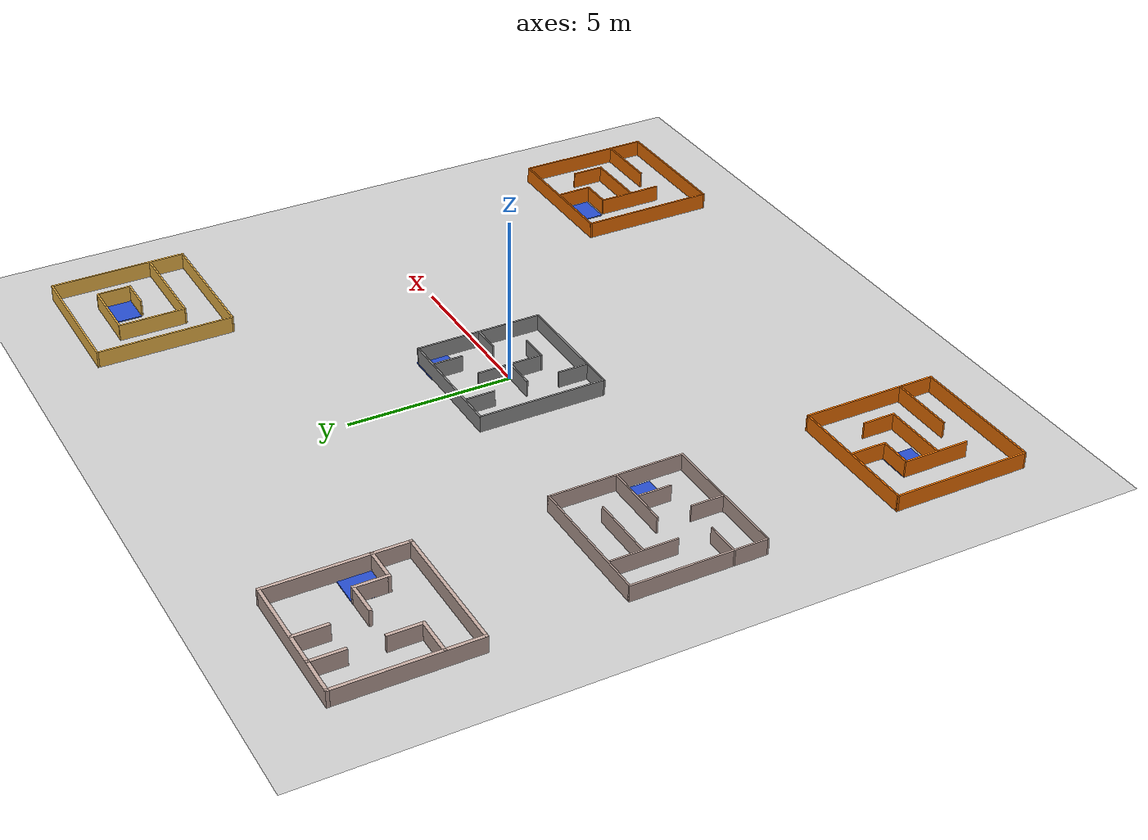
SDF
<sdf version="1.6">
 <world name="default">
  <light name="sun" type="directional">
   <pose>0 0 10 0 -0 0</pose>
   <diffuse>0.8 0.8 0.8 1</diffuse>
   <specular>0.1 0.1 0.1 1</specular>
   <attenuation>
    <range>1000</range>
    <constant>0.9</constant>
    <linear>0.01</linear>
    <quadratic>0.001</quadratic>
   </attenuation>
   <direction>-0.5 0.5 -1</direction>
  </light>
  <model name="ground_plane">
   <static>1</static>
   <link name="link">
    <collision name="collision">
     <geometry><plane><normal>0 0 1</normal><size>100 100</size></plane></geometry>
     <surface><friction><ode><mu>100</mu><mu2>50</mu2></ode></friction></surface>
    </collision>
    <visual name="visual">
     <cast_shadows>0</cast_shadows>
     <geometry><plane><normal>0 0 1</normal><size>100 100</size></plane></geometry>
     <material>
      <script><uri>file://media/materials/scripts/gazebo.material</uri><name>Gazebo/Grey</name></script>
     </material>
    </visual>
   </link>
  </model>
  <gravity>0 0 -9.8</gravity>
  <magnetic_field>6e-06 2.3e-05 -4.2e-05</magnetic_field>
  <atmosphere type="adiabatic"/>
  <physics name="default_physics" default="0" type="ode">
   <max_step_size>0.001</max_step_size>
   <real_time_factor>1</real_time_factor>
   <real_time_update_rate>1000</real_time_update_rate>
  </physics>
  <scene><ambient>0.4 0.4 0.4 1</ambient><background>0.7 0.7 0.7 1</background><shadows>1</shadows></scene>
  <spherical_coordinates>
   <surface_model>EARTH_WGS84</surface_model>
   <latitude_deg>0</latitude_deg>
   <longitude_deg>0</longitude_deg>
   <elevation>0</elevation>
   <heading_deg>0</heading_deg>
  </spherical_coordinates>
  <model name="maze-one_0">
   <link name="Wall_11">
    <pose>0 1.925 0 0 -0 0</pose>
    <visual name="Wall_11_Visual">
     <pose>0 0 0.25 0 -0 0</pose>
     <geometry><box><size>3.9 0.05 0.5</size></box></geometry>
     <material>
      <script><uri>file://media/materials/scripts/gazebo.material</uri><name>Gazebo/Grey</name></script>
      <ambient>1 1 1 1</ambient>
      <diffuse>0.7 0.7 0.7 1</diffuse>
      <specular>0.01 0.01 0.01 1</specular>
      <emissive>0 0 0 1</emissive>
     </material>
    </visual>
    <collision name="Wall_11_Collision">
     <pose>0 0 0.25 0 -0 0</pose>
     <geometry><box><size>3.9 0.05 0.5</size></box></geometry>
     <surface>
      <friction>
       <ode><mu>1</mu><mu2>1</mu2><fdir1>0 0 0</fdir1><slip1>0</slip1><slip2>0</slip2></ode>
       <torsional>
        <coefficient>1</coefficient>
        <patch_radius>0</patch_radius>
        <surface_radius>0</surface_radius>
        <use_patch_radius>1</use_patch_radius>
        <ode><slip>0</slip></ode>
       </torsional>
      </friction>
      <bounce><restitution_coefficient>0</restitution_coefficient><threshold>1e+06</threshold></bounce>
      <contact>
       <collide_without_contact>0</collide_without_contact>
       <collide_without_contact_bitmask>1</collide_without_contact_bitmask>
       <collide_bitmask>1</collide_bitmask>
       <ode>
        <soft_cfm>0</soft_cfm>
        <soft_erp>0.2</soft_erp>
        <kp>1e+13</kp>
        <kd>1</kd>
        <max_vel>0.01</max_vel>
        <min_depth>0</min_depth>
       </ode>
       <bullet>
        <split_impulse>1</split_impulse>
        <split_impulse_penetration_threshold>-0.01</split_impulse_penetration_threshold>
        <soft_cfm>0</soft_cfm>
        <soft_erp>0.2</soft_erp>
        <kp>1e+13</kp>
        <kd>1</kd>
       </bullet>
      </contact>
     </surface>
    </collision>
   </link>
   <link name="Wall_12">
    <pose>1.925 0 0 0 0 -1.5708</pose>
    <visual name="Wall_12_Visual">
     <pose>0 0 0.25 0 -0 0</pose>
     <geometry><box><size>3.9 0.05 0.5</size></box></geometry>
     <material>
      <script><uri>file://media/materials/scripts/gazebo.material</uri><name>Gazebo/Grey</name></script>
      <ambient>1 1 1 1</ambient>
      <diffuse>0.7 0.7 0.7 1</diffuse>
      <specular>0.01 0.01 0.01 1</specular>
      <emissive>0 0 0 1</emissive>
     </material>
    </visual>
    <collision name="Wall_12_Collision">
     <pose>0 0 0.25 0 -0 0</pose>
     <geometry><box><size>3.9 0.05 0.5</size></box></geometry>
     <surface>
      <friction>
       <ode><mu>1</mu><mu2>1</mu2><fdir1>0 0 0</fdir1><slip1>0</slip1><slip2>0</slip2></ode>
       <torsional>
        <coefficient>1</coefficient>
        <patch_radius>0</patch_radius>
        <surface_radius>0</surface_radius>
        <use_patch_radius>1</use_patch_radius>
        <ode><slip>0</slip></ode>
       </torsional>
      </friction>
      <bounce><restitution_coefficient>0</restitution_coefficient><threshold>1e+06</threshold></bounce>
      <contact>
       <collide_without_contact>0</collide_without_contact>
       <collide_without_contact_bitmask>1</collide_without_contact_bitmask>
       <collide_bitmask>1</collide_bitmask>
       <ode>
        <soft_cfm>0</soft_cfm>
        <soft_erp>0.2</soft_erp>
        <kp>1e+13</kp>
        <kd>1</kd>
        <max_vel>0.01</max_vel>
        <min_depth>0</min_depth>
       </ode>
       <bullet>
        <split_impulse>1</split_impulse>
        <split_impulse_penetration_threshold>-0.01</split_impulse_penetration_threshold>
        <soft_cfm>0</soft_cfm>
        <soft_erp>0.2</soft_erp>
        <kp>1e+13</kp>
        <kd>1</kd>
       </bullet>
      </contact>
     </surface>
    </collision>
   </link>
   <link name="Wall_13">
    <pose>0 -1.925 0 0 -0 3.14159</pose>
    <visual name="Wall_13_Visual">
     <pose>0 0 0.25 0 -0 0</pose>
     <geometry><box><size>3.9 0.05 0.5</size></box></geometry>
     <material>
      <script><uri>file://media/materials/scripts/gazebo.material</uri><name>Gazebo/Grey</name></script>
      <ambient>1 1 1 1</ambient>
      <diffuse>0.7 0.7 0.7 1</diffuse>
      <specular>0.01 0.01 0.01 1</specular>
      <emissive>0 0 0 1</emissive>
     </material>
    </visual>
    <collision name="Wall_13_Collision">
     <pose>0 0 0.25 0 -0 0</pose>
     <geometry><box><size>3.9 0.05 0.5</size></box></geometry>
     <surface>
      <friction>
       <ode><mu>1</mu><mu2>1</mu2><fdir1>0 0 0</fdir1><slip1>0</slip1><slip2>0</slip2></ode>
       <torsional>
        <coefficient>1</coefficient>
        <patch_radius>0</patch_radius>
        <surface_radius>0</surface_radius>
        <use_patch_radius>1</use_patch_radius>
        <ode><slip>0</slip></ode>
       </torsional>
      </friction>
      <bounce><restitution_coefficient>0</restitution_coefficient><threshold>1e+06</threshold></bounce>
      <contact>
       <collide_without_contact>0</collide_without_contact>
       <collide_without_contact_bitmask>1</collide_without_contact_bitmask>
       <collide_bitmask>1</collide_bitmask>
       <ode>
        <soft_cfm>0</soft_cfm>
        <soft_erp>0.2</soft_erp>
        <kp>1e+13</kp>
        <kd>1</kd>
        <max_vel>0.01</max_vel>
        <min_depth>0</min_depth>
       </ode>
       <bullet>
        <split_impulse>1</split_impulse>
        <split_impulse_penetration_threshold>-0.01</split_impulse_penetration_threshold>
        <soft_cfm>0</soft_cfm>
        <soft_erp>0.2</soft_erp>
        <kp>1e+13</kp>
        <kd>1</kd>
       </bullet>
      </contact>
     </surface>
    </collision>
   </link>
   <link name="Wall_14">
    <pose>-1.925 0 0 0 -0 1.5708</pose>
    <visual name="Wall_14_Visual">
     <pose>0 0 0.25 0 -0 0</pose>
     <geometry><box><size>3.9 0.05 0.5</size></box></geometry>
     <material>
      <script><uri>file://media/materials/scripts/gazebo.material</uri><name>Gazebo/Grey</name></script>
      <ambient>1 1 1 1</ambient>
      <diffuse>0.7 0.7 0.7 1</diffuse>
      <specular>0.01 0.01 0.01 1</specular>
      <emissive>0 0 0 1</emissive>
     </material>
    </visual>
    <collision name="Wall_14_Collision">
     <pose>0 0 0.25 0 -0 0</pose>
     <geometry><box><size>3.9 0.05 0.5</size></box></geometry>
     <surface>
      <friction>
       <ode><mu>1</mu><mu2>1</mu2><fdir1>0 0 0</fdir1><slip1>0</slip1><slip2>0</slip2></ode>
       <torsional>
        <coefficient>1</coefficient>
        <patch_radius>0</patch_radius>
        <surface_radius>0</surface_radius>
        <use_patch_radius>1</use_patch_radius>
        <ode><slip>0</slip></ode>
       </torsional>
      </friction>
      <bounce><restitution_coefficient>0</restitution_coefficient><threshold>1e+06</threshold></bounce>
      <contact>
       <collide_without_contact>0</collide_without_contact>
       <collide_without_contact_bitmask>1</collide_without_contact_bitmask>
       <collide_bitmask>1</collide_bitmask>
       <ode>
        <soft_cfm>0</soft_cfm>
        <soft_erp>0.2</soft_erp>
        <kp>1e+13</kp>
        <kd>1</kd>
        <max_vel>0.01</max_vel>
        <min_depth>0</min_depth>
       </ode>
       <bullet>
        <split_impulse>1</split_impulse>
        <split_impulse_penetration_threshold>-0.01</split_impulse_penetration_threshold>
        <soft_cfm>0</soft_cfm>
        <soft_erp>0.2</soft_erp>
        <kp>1e+13</kp>
        <kd>1</kd>
       </bullet>
      </contact>
     </surface>
    </collision>
   </link>
   <link name="Wall_27">
    <pose>0.996 1.4547 0 0 0 -1.5708</pose>
    <visual name="Wall_27_Visual">
     <pose>0 0 0.25 0 -0 0</pose>
     <geometry><box><size>0.900337 0.05 0.5</size></box></geometry>
     <material>
      <script><uri>file://media/materials/scripts/gazebo.material</uri><name>Gazebo/Grey</name></script>
      <ambient>1 1 1 1</ambient>
      <diffuse>0.7 0.7 0.7 1</diffuse>
      <specular>0.01 0.01 0.01 1</specular>
      <emissive>0 0 0 1</emissive>
     </material>
    </visual>
    <collision name="Wall_27_Collision">
     <pose>0 0 0.25 0 -0 0</pose>
     <geometry><box><size>0.900337 0.05 0.5</size></box></geometry>
     <surface>
      <friction>
       <ode><mu>1</mu><mu2>1</mu2><fdir1>0 0 0</fdir1><slip1>0</slip1><slip2>0</slip2></ode>
       <torsional>
        <coefficient>1</coefficient>
        <patch_radius>0</patch_radius>
        <surface_radius>0</surface_radius>
        <use_patch_radius>1</use_patch_radius>
        <ode><slip>0</slip></ode>
       </torsional>
      </friction>
      <bounce><restitution_coefficient>0</restitution_coefficient><threshold>1e+06</threshold></bounce>
      <contact>
       <collide_without_contact>0</collide_without_contact>
       <collide_without_contact_bitmask>1</collide_without_contact_bitmask>
       <collide_bitmask>1</collide_bitmask>
       <ode>
        <soft_cfm>0</soft_cfm>
        <soft_erp>0.2</soft_erp>
        <kp>1e+13</kp>
        <kd>1</kd>
        <max_vel>0.01</max_vel>
        <min_depth>0</min_depth>
       </ode>
       <bullet>
        <split_impulse>1</split_impulse>
        <split_impulse_penetration_threshold>-0.01</split_impulse_penetration_threshold>
        <soft_cfm>0</soft_cfm>
        <soft_erp>0.2</soft_erp>
        <kp>1e+13</kp>
        <kd>1</kd>
       </bullet>
      </contact>
     </surface>
    </collision>
   </link>
   <link name="Wall_30">
    <pose>-1.0002 1.4523 0 0 0 -1.5708</pose>
    <visual name="Wall_30_Visual">
     <pose>0 0 0.25 0 -0 0</pose>
     <geometry><box><size>0.900217 0.05 0.5</size></box></geometry>
     <material>
      <script><uri>file://media/materials/scripts/gazebo.material</uri><name>Gazebo/Grey</name></script>
      <ambient>1 1 1 1</ambient>
      <diffuse>0.7 0.7 0.7 1</diffuse>
      <specular>0.01 0.01 0.01 1</specular>
      <emissive>0 0 0 1</emissive>
     </material>
    </visual>
    <collision name="Wall_30_Collision">
     <pose>0 0 0.25 0 -0 0</pose>
     <geometry><box><size>0.900217 0.05 0.5</size></box></geometry>
     <surface>
      <friction>
       <ode><mu>1</mu><mu2>1</mu2><fdir1>0 0 0</fdir1><slip1>0</slip1><slip2>0</slip2></ode>
       <torsional>
        <coefficient>1</coefficient>
        <patch_radius>0</patch_radius>
        <surface_radius>0</surface_radius>
        <use_patch_radius>1</use_patch_radius>
        <ode><slip>0</slip></ode>
       </torsional>
      </friction>
      <bounce><restitution_coefficient>0</restitution_coefficient><threshold>1e+06</threshold></bounce>
      <contact>
       <collide_without_contact>0</collide_without_contact>
       <collide_without_contact_bitmask>1</collide_without_contact_bitmask>
       <collide_bitmask>1</collide_bitmask>
       <ode>
        <soft_cfm>0</soft_cfm>
        <soft_erp>0.2</soft_erp>
        <kp>1e+13</kp>
        <kd>1</kd>
        <max_vel>0.01</max_vel>
        <min_depth>0</min_depth>
       </ode>
       <bullet>
        <split_impulse>1</split_impulse>
        <split_impulse_penetration_threshold>-0.01</split_impulse_penetration_threshold>
        <soft_cfm>0</soft_cfm>
        <soft_erp>0.2</soft_erp>
        <kp>1e+13</kp>
        <kd>1</kd>
       </bullet>
      </contact>
     </surface>
    </collision>
   </link>
   <link name="Wall_36">
    <pose>1.48944 0.002482 0 0 -0 3.14159</pose>
    <visual name="Wall_36_Visual">
     <pose>0 0 0.25 0 -0 0</pose>
     <geometry><box><size>0.9 0.05 0.5</size></box></geometry>
     <material>
      <script><uri>file://media/materials/scripts/gazebo.material</uri><name>Gazebo/Grey</name></script>
      <ambient>1 1 1 1</ambient>
      <diffuse>0.7 0.7 0.7 1</diffuse>
      <specular>0.01 0.01 0.01 1</specular>
      <emissive>0 0 0 1</emissive>
     </material>
    </visual>
    <collision name="Wall_36_Collision">
     <pose>0 0 0.25 0 -0 0</pose>
     <geometry><box><size>0.9 0.05 0.5</size></box></geometry>
     <surface>
      <friction>
       <ode><mu>1</mu><mu2>1</mu2><fdir1>0 0 0</fdir1><slip1>0</slip1><slip2>0</slip2></ode>
       <torsional>
        <coefficient>1</coefficient>
        <patch_radius>0</patch_radius>
        <surface_radius>0</surface_radius>
        <use_patch_radius>1</use_patch_radius>
        <ode><slip>0</slip></ode>
       </torsional>
      </friction>
      <bounce><restitution_coefficient>0</restitution_coefficient><threshold>1e+06</threshold></bounce>
      <contact>
       <collide_without_contact>0</collide_without_contact>
       <collide_without_contact_bitmask>1</collide_without_contact_bitmask>
       <collide_bitmask>1</collide_bitmask>
       <ode>
        <soft_cfm>0</soft_cfm>
        <soft_erp>0.2</soft_erp>
        <kp>1e+13</kp>
        <kd>1</kd>
        <max_vel>0.01</max_vel>
        <min_depth>0</min_depth>
       </ode>
       <bullet>
        <split_impulse>1</split_impulse>
        <split_impulse_penetration_threshold>-0.01</split_impulse_penetration_threshold>
        <soft_cfm>0</soft_cfm>
        <soft_erp>0.2</soft_erp>
        <kp>1e+13</kp>
        <kd>1</kd>
       </bullet>
      </contact>
     </surface>
    </collision>
   </link>
   <link name="Wall_40">
    <pose>-0.997417 -1.45292 0 0 0 -1.5708</pose>
    <visual name="Wall_40_Visual">
     <pose>0 0 0.25 0 -0 0</pose>
     <geometry><box><size>0.899931 0.05 0.5</size></box></geometry>
     <material>
      <script><uri>file://media/materials/scripts/gazebo.material</uri><name>Gazebo/Grey</name></script>
      <ambient>1 1 1 1</ambient>
      <diffuse>0.7 0.7 0.7 1</diffuse>
      <specular>0.01 0.01 0.01 1</specular>
      <emissive>0 0 0 1</emissive>
     </material>
    </visual>
    <collision name="Wall_40_Collision">
     <pose>0 0 0.25 0 -0 0</pose>
     <geometry><box><size>0.899931 0.05 0.5</size></box></geometry>
     <surface>
      <friction>
       <ode><mu>1</mu><mu2>1</mu2><fdir1>0 0 0</fdir1><slip1>0</slip1><slip2>0</slip2></ode>
       <torsional>
        <coefficient>1</coefficient>
        <patch_radius>0</patch_radius>
        <surface_radius>0</surface_radius>
        <use_patch_radius>1</use_patch_radius>
        <ode><slip>0</slip></ode>
       </torsional>
      </friction>
      <bounce><restitution_coefficient>0</restitution_coefficient><threshold>1e+06</threshold></bounce>
      <contact>
       <collide_without_contact>0</collide_without_contact>
       <collide_without_contact_bitmask>1</collide_without_contact_bitmask>
       <collide_bitmask>1</collide_bitmask>
       <ode>
        <soft_cfm>0</soft_cfm>
        <soft_erp>0.2</soft_erp>
        <kp>1e+13</kp>
        <kd>1</kd>
        <max_vel>0.01</max_vel>
        <min_depth>0</min_depth>
       </ode>
       <bullet>
        <split_impulse>1</split_impulse>
        <split_impulse_penetration_threshold>-0.01</split_impulse_penetration_threshold>
        <soft_cfm>0</soft_cfm>
        <soft_erp>0.2</soft_erp>
        <kp>1e+13</kp>
        <kd>1</kd>
       </bullet>
      </contact>
     </surface>
    </collision>
   </link>
   <link name="Wall_43">
    <pose>-0.496076 -0.00777 0 0 -0 3.14159</pose>
    <inertial>
     <inertia><ixx>nan</ixx><ixy>0</ixy><ixz>0</ixz><iyy>nan</iyy><iyz>0</iyz><izz>nan</izz></inertia>
     <mass>0</mass>
    </inertial>
    <visual name="Wall_43_Visual">
     <pose>0 0 0.25 0 -0 0</pose>
     <geometry><box><size>1.0129 0.05 0.5</size></box></geometry>
     <material>
      <script><uri>file://media/materials/scripts/gazebo.material</uri><name>Gazebo/Grey</name></script>
      <ambient>1 1 1 1</ambient>
      <diffuse>0.7 0.7 0.7 1</diffuse>
      <specular>0.01 0.01 0.01 1</specular>
      <emissive>0 0 0 1</emissive>
     </material>
    </visual>
    <collision name="Wall_43_Collision">
     <pose>0 0 0.25 0 -0 0</pose>
     <geometry><box><size>1.0129 0.05 0.5</size></box></geometry>
     <surface>
      <friction>
       <ode><mu>1</mu><mu2>1</mu2><fdir1>0 0 0</fdir1><slip1>0</slip1><slip2>0</slip2></ode>
       <torsional>
        <coefficient>1</coefficient>
        <patch_radius>0</patch_radius>
        <surface_radius>0</surface_radius>
        <use_patch_radius>1</use_patch_radius>
        <ode><slip>0</slip></ode>
       </torsional>
      </friction>
      <bounce><restitution_coefficient>0</restitution_coefficient><threshold>1e+06</threshold></bounce>
      <contact>
       <collide_without_contact>0</collide_without_contact>
       <collide_without_contact_bitmask>1</collide_without_contact_bitmask>
       <collide_bitmask>1</collide_bitmask>
       <ode>
        <soft_cfm>0</soft_cfm>
        <soft_erp>0.2</soft_erp>
        <kp>1e+13</kp>
        <kd>1</kd>
        <max_vel>0.01</max_vel>
        <min_depth>0</min_depth>
       </ode>
       <bullet>
        <split_impulse>1</split_impulse>
        <split_impulse_penetration_threshold>-0.01</split_impulse_penetration_threshold>
        <soft_cfm>0</soft_cfm>
        <soft_erp>0.2</soft_erp>
        <kp>1e+13</kp>
        <kd>1</kd>
       </bullet>
      </contact>
     </surface>
    </collision>
   </link>
   <link name="Wall_45">
    <pose>0.004129 0.508535 0 0 -0 1.5708</pose>
    <inertial>
     <mass>1.05671</mass>
     <inertia><ixx>1.05671</ixx><ixy>0</ixy><ixz>0</ixz><iyy>1.11833</iyy><iyz>0</iyz><izz>1.11833</izz></inertia>
    </inertial>
    <visual name="Wall_45_Visual">
     <pose>0 0 0.25 0 -0 0</pose>
     <geometry><box><size>0.990985 0.05 0.5</size></box></geometry>
     <material>
      <script><uri>file://media/materials/scripts/gazebo.material</uri><name>Gazebo/Grey</name></script>
      <ambient>1 1 1 1</ambient>
      <diffuse>0.7 0.7 0.7 1</diffuse>
      <specular>0.01 0.01 0.01 1</specular>
      <emissive>0 0 0 1</emissive>
      <shader type="vertex"><normal_map>__default__</normal_map></shader>
     </material>
    </visual>
    <collision name="Wall_45_Collision">
     <pose>0 0 0.25 0 -0 0</pose>
     <geometry><box><size>0.990985 0.05 0.5</size></box></geometry>
     <surface>
      <friction>
       <ode><mu>1</mu><mu2>1</mu2><fdir1>0 0 0</fdir1><slip1>0</slip1><slip2>0</slip2></ode>
       <torsional>
        <coefficient>1</coefficient>
        <patch_radius>0</patch_radius>
        <surface_radius>0</surface_radius>
        <use_patch_radius>1</use_patch_radius>
        <ode><slip>0</slip></ode>
       </torsional>
      </friction>
      <bounce><restitution_coefficient>0</restitution_coefficient><threshold>1e+06</threshold></bounce>
      <contact>
       <collide_without_contact>0</collide_without_contact>
       <collide_without_contact_bitmask>1</collide_without_contact_bitmask>
       <collide_bitmask>1</collide_bitmask>
       <ode>
        <soft_cfm>0</soft_cfm>
        <soft_erp>0.2</soft_erp>
        <kp>1e+13</kp>
        <kd>1</kd>
        <max_vel>0.01</max_vel>
        <min_depth>0</min_depth>
       </ode>
       <bullet>
        <split_impulse>1</split_impulse>
        <split_impulse_penetration_threshold>-0.01</split_impulse_penetration_threshold>
        <soft_cfm>0</soft_cfm>
        <soft_erp>0.2</soft_erp>
        <kp>1e+13</kp>
        <kd>1</kd>
       </bullet>
      </contact>
     </surface>
    </collision>
   </link>
   <link name="Wall_47">
    <pose>0.003706 -0.469247 0 0 0 -1.5708</pose>
    <inertial>
     <inertia><ixx>nan</ixx><ixy>0</ixy><ixz>0</ixz><iyy>nan</iyy><iyz>0</iyz><izz>nan</izz></inertia>
     <mass>0</mass>
    </inertial>
    <visual name="Wall_47_Visual">
     <pose>0 0 0.25 0 -0 0</pose>
     <geometry><box><size>0.992125 0.05 0.5</size></box></geometry>
     <material>
      <script><uri>file://media/materials/scripts/gazebo.material</uri><name>Gazebo/Grey</name></script>
      <ambient>1 1 1 1</ambient>
      <diffuse>0.7 0.7 0.7 1</diffuse>
      <specular>0.01 0.01 0.01 1</specular>
      <emissive>0 0 0 1</emissive>
     </material>
    </visual>
    <collision name="Wall_47_Collision">
     <pose>0 0 0.25 0 -0 0</pose>
     <geometry><box><size>0.992125 0.05 0.5</size></box></geometry>
     <surface>
      <friction>
       <ode><mu>1</mu><mu2>1</mu2><fdir1>0 0 0</fdir1><slip1>0</slip1><slip2>0</slip2></ode>
       <torsional>
        <coefficient>1</coefficient>
        <patch_radius>0</patch_radius>
        <surface_radius>0</surface_radius>
        <use_patch_radius>1</use_patch_radius>
        <ode><slip>0</slip></ode>
       </torsional>
      </friction>
      <bounce><restitution_coefficient>0</restitution_coefficient><threshold>1e+06</threshold></bounce>
      <contact>
       <collide_without_contact>0</collide_without_contact>
       <collide_without_contact_bitmask>1</collide_without_contact_bitmask>
       <collide_bitmask>1</collide_bitmask>
       <ode>
        <soft_cfm>0</soft_cfm>
        <soft_erp>0.2</soft_erp>
        <kp>1e+13</kp>
        <kd>1</kd>
        <max_vel>0.01</max_vel>
        <min_depth>0</min_depth>
       </ode>
       <bullet>
        <split_impulse>1</split_impulse>
        <split_impulse_penetration_threshold>-0.01</split_impulse_penetration_threshold>
        <soft_cfm>0</soft_cfm>
        <soft_erp>0.2</soft_erp>
        <kp>1e+13</kp>
        <kd>1</kd>
       </bullet>
      </contact>
     </surface>
    </collision>
   </link>
   <link name="Wall_49">
    <pose>0.431063 -0.987023 0 0 -0 0</pose>
    <visual name="Wall_49_Visual">
     <pose>0 0 0.25 0 -0 0</pose>
     <geometry><box><size>0.900077 0.05 0.5</size></box></geometry>
     <material>
      <script><uri>file://media/materials/scripts/gazebo.material</uri><name>Gazebo/Grey</name></script>
      <ambient>1 1 1 1</ambient>
      <diffuse>0.7 0.7 0.7 1</diffuse>
      <specular>0.01 0.01 0.01 1</specular>
      <emissive>0 0 0 1</emissive>
     </material>
    </visual>
    <collision name="Wall_49_Collision">
     <pose>0 0 0.25 0 -0 0</pose>
     <geometry><box><size>0.900077 0.05 0.5</size></box></geometry>
     <surface>
      <friction>
       <ode><mu>1</mu><mu2>1</mu2><fdir1>0 0 0</fdir1><slip1>0</slip1><slip2>0</slip2></ode>
       <torsional>
        <coefficient>1</coefficient>
        <patch_radius>0</patch_radius>
        <surface_radius>0</surface_radius>
        <use_patch_radius>1</use_patch_radius>
        <ode><slip>0</slip></ode>
       </torsional>
      </friction>
      <bounce><restitution_coefficient>0</restitution_coefficient><threshold>1e+06</threshold></bounce>
      <contact>
       <collide_without_contact>0</collide_without_contact>
       <collide_without_contact_bitmask>1</collide_without_contact_bitmask>
       <collide_bitmask>1</collide_bitmask>
       <ode>
        <soft_cfm>0</soft_cfm>
        <soft_erp>0.2</soft_erp>
        <kp>1e+13</kp>
        <kd>1</kd>
        <max_vel>0.01</max_vel>
        <min_depth>0</min_depth>
       </ode>
       <bullet>
        <split_impulse>1</split_impulse>
        <split_impulse_penetration_threshold>-0.01</split_impulse_penetration_threshold>
        <soft_cfm>0</soft_cfm>
        <soft_erp>0.2</soft_erp>
        <kp>1e+13</kp>
        <kd>1</kd>
       </bullet>
      </contact>
     </surface>
    </collision>
   </link>
   <static>1</static>
  </model>
  <model name="maze-two">
   <pose>-8.05 7.98 0 0 -0 0</pose>
   <link name="Wall_14">
    <collision name="Wall_14_Collision">
     <geometry><box><size>4.20038 0.1 0.5</size></box></geometry>
     <pose>0 0 0.25 0 -0 0</pose>
    </collision>
    <visual name="Wall_14_Visual">
     <pose>0 0 0.25 0 -0 0</pose>
     <geometry><box><size>4.20038 0.1 0.5</size></box></geometry>
     <material>
      <script><uri>file://media/materials/scripts/gazebo.material</uri><name>Gazebo/Grey</name></script>
      <ambient>0.760784 0.662745 0.627451 1</ambient>
     </material>
    </visual>
    <pose>2.05 0 0 0 0 -1.5708</pose>
   </link>
   <link name="Wall_15">
    <collision name="Wall_15_Collision">
     <geometry><box><size>4.19965 0.1 0.5</size></box></geometry>
     <pose>0 0 0.25 0 -0 0</pose>
    </collision>
    <visual name="Wall_15_Visual">
     <pose>0 0 0.25 0 -0 0</pose>
     <geometry><box><size>4.19965 0.1 0.5</size></box></geometry>
     <material>
      <script><uri>file://media/materials/scripts/gazebo.material</uri><name>Gazebo/Grey</name></script>
      <ambient>0.760784 0.662745 0.627451 1</ambient>
     </material>
    </visual>
    <pose>0 -2.05 0 0 -0 3.14159</pose>
   </link>
   <link name="Wall_16">
    <collision name="Wall_16_Collision">
     <geometry><box><size>4.2 0.1 0.5</size></box></geometry>
     <pose>0 0 0.25 0 -0 0</pose>
    </collision>
    <visual name="Wall_16_Visual">
     <pose>0 0 0.25 0 -0 0</pose>
     <geometry><box><size>4.2 0.1 0.5</size></box></geometry>
     <material>
      <script><uri>file://media/materials/scripts/gazebo.material</uri><name>Gazebo/Grey</name></script>
      <ambient>0.760784 0.662745 0.627451 1</ambient>
     </material>
    </visual>
    <pose>-2.05 0 0 0 -0 1.5708</pose>
   </link>
   <link name="Wall_18">
    <collision name="Wall_18_Collision">
     <geometry><box><size>4.20036 0.1 0.5</size></box></geometry>
     <pose>0 0 0.25 0 -0 0</pose>
    </collision>
    <visual name="Wall_18_Visual">
     <pose>0 0 0.25 0 -0 0</pose>
     <geometry><box><size>4.20036 0.1 0.5</size></box></geometry>
     <material>
      <script><uri>file://media/materials/scripts/gazebo.material</uri><name>Gazebo/Grey</name></script>
      <ambient>0.760784 0.662745 0.627451 1</ambient>
     </material>
    </visual>
    <pose>0 2.05 0 0 -0 0</pose>
   </link>
   <link name="Wall_27">
    <collision name="Wall_27_Collision">
     <geometry><box><size>1.201 0.1 0.5</size></box></geometry>
     <pose>0 0 0.25 0 -0 0</pose>
    </collision>
    <visual name="Wall_27_Visual">
     <pose>0 0 0.25 0 -0 0</pose>
     <geometry><box><size>1.201 0.1 0.5</size></box></geometry>
     <material>
      <script><uri>file://media/materials/scripts/gazebo.material</uri><name>Gazebo/Grey</name></script>
      <ambient>0.760784 0.662745 0.627451 1</ambient>
     </material>
    </visual>
    <pose>-1.4855 -0.955 0 0 -0 0</pose>
   </link>
   <link name="Wall_29">
    <collision name="Wall_29_Collision">
     <geometry><box><size>1.05 0.1 0.5</size></box></geometry>
     <pose>0 0 0.25 0 -0 0</pose>
    </collision>
    <visual name="Wall_29_Visual">
     <pose>0 0 0.25 0 -0 0</pose>
     <geometry><box><size>1.05 0.1 0.5</size></box></geometry>
     <material>
      <script><uri>file://media/materials/scripts/gazebo.material</uri><name>Gazebo/Grey</name></script>
      <ambient>0.760784 0.662745 0.627451 1</ambient>
     </material>
    </visual>
    <pose>-0.935 -0.48 0 0 -0 1.5708</pose>
   </link>
   <link name="Wall_31">
    <collision name="Wall_31_Collision">
     <geometry><box><size>1.06 0.1 0.5</size></box></geometry>
     <pose>0 0 0.25 0 -0 0</pose>
    </collision>
    <visual name="Wall_31_Visual">
     <pose>0 0 0.25 0 -0 0</pose>
     <geometry><box><size>1.06 0.1 0.5</size></box></geometry>
     <material>
      <script><uri>file://media/materials/scripts/gazebo.material</uri><name>Gazebo/Grey</name></script>
      <ambient>0.760784 0.662745 0.627451 1</ambient>
     </material>
    </visual>
    <pose>1.545 -0.973 0 0 -0 3.14159</pose>
   </link>
   <link name="Wall_33">
    <collision name="Wall_33_Collision">
     <geometry><box><size>1.05 0.1 0.5</size></box></geometry>
     <pose>0 0 0.25 0 -0 0</pose>
    </collision>
    <visual name="Wall_33_Visual">
     <pose>0 0 0.25 0 -0 0</pose>
     <geometry><box><size>1.05 0.1 0.5</size></box></geometry>
     <material>
      <script><uri>file://media/materials/scripts/gazebo.material</uri><name>Gazebo/Grey</name></script>
      <ambient>0.760784 0.662745 0.627451 1</ambient>
     </material>
    </visual>
    <pose>1.065 -0.498 0 0 -0 1.5708</pose>
   </link>
   <link name="Wall_35">
    <collision name="Wall_35_Collision">
     <geometry><box><size>1.05 0.1 0.5</size></box></geometry>
     <pose>0 0 0.25 0 -0 0</pose>
    </collision>
    <visual name="Wall_35_Visual">
     <pose>0 0 0.25 0 -0 0</pose>
     <geometry><box><size>1.05 0.1 0.5</size></box></geometry>
     <material>
      <script><uri>file://media/materials/scripts/gazebo.material</uri><name>Gazebo/Grey</name></script>
      <ambient>0.760784 0.662745 0.627451 1</ambient>
     </material>
    </visual>
    <pose>0.59 -0.023 0 0 -0 3.14159</pose>
   </link>
   <link name="Wall_41">
    <collision name="Wall_41_Collision">
     <geometry><box><size>1.06 0.1 0.5</size></box></geometry>
     <pose>0 0 0.25 0 -0 0</pose>
    </collision>
    <visual name="Wall_41_Visual">
     <pose>0 0 0.25 0 -0 0</pose>
     <geometry><box><size>1.06 0.1 0.5</size></box></geometry>
     <material>
      <script><uri>file://media/materials/scripts/gazebo.material</uri><name>Gazebo/Grey</name></script>
      <ambient>0.760784 0.662745 0.627451 1</ambient>
     </material>
    </visual>
    <pose>-0.935 1.565 0 0 -0 1.5708</pose>
   </link>
   <link name="Wall_44">
    <collision name="Wall_44_Collision">
     <geometry><box><size>1.05 0.1 0.5</size></box></geometry>
     <pose>0 0 0.25 0 -0 0</pose>
    </collision>
    <visual name="Wall_44_Visual">
     <pose>0 0 0.25 0 -0 0</pose>
     <geometry><box><size>1.05 0.1 0.5</size></box></geometry>
     <material>
      <script><uri>file://media/materials/scripts/gazebo.material</uri><name>Gazebo/Grey</name></script>
      <ambient>0.760784 0.662745 0.627451 1</ambient>
     </material>
    </visual>
    <pose>0.065 1.552 0 0 -0 1.5708</pose>
   </link>
   <static>1</static>
  </model>
  <model name="maze-six">
   <pose>7.99961 8.01527 0 0 -0 0</pose>
   <link name="Wall_51">
    <collision name="Wall_51_Collision">
     <geometry><box><size>4.14 0.05 0.5</size></box></geometry>
     <pose>0 0 0.25 0 -0 0</pose>
    </collision>
    <visual name="Wall_51_Visual">
     <pose>0 0 0.25 0 -0 0</pose>
     <geometry><box><size>4.14 0.05 0.5</size></box></geometry>
     <material>
      <script><uri>file://media/materials/scripts/gazebo.material</uri><name>Gazebo/Grey</name></script>
      <ambient>1 0.764706 0.305882 1</ambient>
     </material>
    </visual>
    <pose>-2.05 0 0 0 0 -1.5708</pose>
   </link>
   <link name="Wall_53">
    <collision name="Wall_53_Collision">
     <geometry><box><size>4.15037 0.05 0.5</size></box></geometry>
     <pose>0 0 0.25 0 -0 0</pose>
    </collision>
    <visual name="Wall_53_Visual">
     <pose>0 0 0.25 0 -0 0</pose>
     <geometry><box><size>4.15037 0.05 0.5</size></box></geometry>
     <material>
      <script><uri>file://media/materials/scripts/gazebo.material</uri><name>Gazebo/Grey</name></script>
      <ambient>1 0.764706 0.305882 1</ambient>
     </material>
    </visual>
    <pose>0 -2.045 0 0 -0 0</pose>
   </link>
   <link name="Wall_54">
    <collision name="Wall_54_Collision">
     <geometry><box><size>4.13975 0.05 0.5</size></box></geometry>
     <pose>0 0 0.25 0 -0 0</pose>
    </collision>
    <visual name="Wall_54_Visual">
     <pose>0 0 0.25 0 -0 0</pose>
     <geometry><box><size>4.13975 0.05 0.5</size></box></geometry>
     <material>
      <script><uri>file://media/materials/scripts/gazebo.material</uri><name>Gazebo/Grey</name></script>
      <ambient>1 0.764706 0.305882 1</ambient>
     </material>
    </visual>
    <pose>2.05 0 0 0 -0 1.5708</pose>
   </link>
   <link name="Wall_55">
    <collision name="Wall_55_Collision">
     <geometry><box><size>4.15 0.05 0.5</size></box></geometry>
     <pose>0 0 0.25 0 -0 0</pose>
    </collision>
    <visual name="Wall_55_Visual">
     <pose>0 0 0.25 0 -0 0</pose>
     <geometry><box><size>4.15 0.05 0.5</size></box></geometry>
     <material>
      <script><uri>file://media/materials/scripts/gazebo.material</uri><name>Gazebo/Grey</name></script>
      <ambient>1 0.764706 0.305882 1</ambient>
     </material>
    </visual>
    <pose>0 2.045 0 0 -0 3.14159</pose>
   </link>
   <link name="Wall_59">
    <collision name="Wall_59_Collision">
     <geometry><box><size>3.05 0.05 0.5</size></box></geometry>
     <pose>0 0 0.25 0 -0 0</pose>
    </collision>
    <visual name="Wall_59_Visual">
     <pose>0 0 0.25 0 -0 0</pose>
     <geometry><box><size>3.05 0.05 0.5</size></box></geometry>
     <material>
      <script><uri>file://media/materials/scripts/gazebo.material</uri><name>Gazebo/Grey</name></script>
      <ambient>1 0.764706 0.305882 1</ambient>
     </material>
    </visual>
    <pose>0.526 -0.993 0 0 -0 3.14159</pose>
   </link>
   <link name="Wall_61">
    <collision name="Wall_61_Collision">
     <geometry><box><size>2.05 0.05 0.5</size></box></geometry>
     <pose>0 0 0.25 0 -0 0</pose>
    </collision>
    <visual name="Wall_61_Visual">
     <pose>0 0 0.25 0 -0 0</pose>
     <geometry><box><size>2.05 0.05 0.5</size></box></geometry>
     <material>
      <script><uri>file://media/materials/scripts/gazebo.material</uri><name>Gazebo/Grey</name></script>
      <ambient>1 0.764706 0.305882 1</ambient>
     </material>
    </visual>
    <pose>-0.974 0.007 0 0 -0 1.5708</pose>
   </link>
   <link name="Wall_63">
    <collision name="Wall_63_Collision">
     <geometry><box><size>2 0.05 0.5</size></box></geometry>
     <pose>0 0 0.25 0 -0 0</pose>
    </collision>
    <visual name="Wall_63_Visual">
     <pose>0 0 0.25 0 -0 0</pose>
     <geometry><box><size>2 0.05 0.5</size></box></geometry>
     <material>
      <script><uri>file://media/materials/scripts/gazebo.material</uri><name>Gazebo/Grey</name></script>
      <ambient>1 0.764706 0.305882 1</ambient>
     </material>
    </visual>
    <pose>0.001 1.007 0 0 -0 0</pose>
   </link>
   <link name="Wall_64">
    <collision name="Wall_64_Collision">
     <geometry><box><size>1.05 0.05 0.5</size></box></geometry>
     <pose>0 0 0.25 0 -0 0</pose>
    </collision>
    <visual name="Wall_64_Visual">
     <pose>0 0 0.25 0 -0 0</pose>
     <geometry><box><size>1.05 0.05 0.5</size></box></geometry>
     <material>
      <script><uri>file://media/materials/scripts/gazebo.material</uri><name>Gazebo/Grey</name></script>
      <ambient>1 0.764706 0.305882 1</ambient>
     </material>
    </visual>
    <pose>0.976 0.507 0 0 0 -1.5708</pose>
   </link>
   <link name="Wall_65">
    <collision name="Wall_65_Collision">
     <geometry><box><size>1 0.05 0.5</size></box></geometry>
     <pose>0 0 0.25 0 -0 0</pose>
    </collision>
    <visual name="Wall_65_Visual">
     <pose>0 0 0.25 0 -0 0</pose>
     <geometry><box><size>1 0.05 0.5</size></box></geometry>
     <material>
      <script><uri>file://media/materials/scripts/gazebo.material</uri><name>Gazebo/Grey</name></script>
      <ambient>1 0.764706 0.305882 1</ambient>
     </material>
    </visual>
    <pose>0.501 0.007 0 0 -0 3.14159</pose>
   </link>
   <static>1</static>
  </model>
  <model name="maze-three-four">
   <pose>7.9579 -7.99361 0 0 -0 0</pose>
   <link name="Wall_72">
    <collision name="Wall_72_Collision">
     <geometry><box><size>4.15039 0.05 0.5</size></box></geometry>
     <pose>0 0 0.25 0 -0 0</pose>
    </collision>
    <visual name="Wall_72_Visual">
     <pose>0 0 0.25 0 -0 0</pose>
     <geometry><box><size>4.15039 0.05 0.5</size></box></geometry>
     <material>
      <script><uri>file://media/materials/scripts/gazebo.material</uri><name>Gazebo/Grey</name></script>
      <ambient>0.996078 0.47451 0.0196078 1</ambient>
     </material>
    </visual>
    <pose>0 2.05 0 0 -0 0</pose>
   </link>
   <link name="Wall_74">
    <collision name="Wall_74_Collision">
     <geometry><box><size>4.15 0.05 0.5</size></box></geometry>
     <pose>0 0 0.25 0 -0 0</pose>
    </collision>
    <visual name="Wall_74_Visual">
     <pose>0 0 0.25 0 -0 0</pose>
     <geometry><box><size>4.15 0.05 0.5</size></box></geometry>
     <material>
      <script><uri>file://media/materials/scripts/gazebo.material</uri><name>Gazebo/Grey</name></script>
      <ambient>0.996078 0.47451 0.0196078 1</ambient>
     </material>
    </visual>
    <pose>2.05 0 0 0 0 -1.5708</pose>
   </link>
   <link name="Wall_75">
    <collision name="Wall_75_Collision">
     <geometry><box><size>4.15 0.05 0.5</size></box></geometry>
     <pose>0 0 0.25 0 -0 0</pose>
    </collision>
    <visual name="Wall_75_Visual">
     <pose>0 0 0.25 0 -0 0</pose>
     <geometry><box><size>4.15 0.05 0.5</size></box></geometry>
     <material>
      <script><uri>file://media/materials/scripts/gazebo.material</uri><name>Gazebo/Grey</name></script>
      <ambient>0.996078 0.47451 0.0196078 1</ambient>
     </material>
    </visual>
    <pose>0 -2.05 0 0 -0 3.14159</pose>
   </link>
   <link name="Wall_76">
    <collision name="Wall_76_Collision">
     <geometry><box><size>4.15 0.05 0.5</size></box></geometry>
     <pose>0 0 0.25 0 -0 0</pose>
    </collision>
    <visual name="Wall_76_Visual">
     <pose>0 0 0.25 0 -0 0</pose>
     <geometry><box><size>4.15 0.05 0.5</size></box></geometry>
     <material>
      <script><uri>file://media/materials/scripts/gazebo.material</uri><name>Gazebo/Grey</name></script>
      <ambient>0.996078 0.47451 0.0196078 1</ambient>
     </material>
    </visual>
    <pose>-2.05 0 0 0 -0 1.5708</pose>
   </link>
   <link name="Wall_81">
    <collision name="Wall_81_Collision">
     <geometry><box><size>2 0.05 0.5</size></box></geometry>
     <pose>0 0 0.25 0 -0 0</pose>
    </collision>
    <visual name="Wall_81_Visual">
     <pose>0 0 0.25 0 -0 0</pose>
     <geometry><box><size>2 0.05 0.5</size></box></geometry>
     <material>
      <script><uri>file://media/materials/scripts/gazebo.material</uri><name>Gazebo/Grey</name></script>
      <ambient>0.996078 0.47451 0.0196078 1</ambient>
     </material>
    </visual>
    <pose>1.058 -0.998 0 0 -0 3.14159</pose>
   </link>
   <link name="Wall_86">
    <collision name="Wall_86_Collision">
     <geometry><box><size>2 0.05 0.5</size></box></geometry>
     <pose>0 0 0.25 0 -0 0</pose>
    </collision>
    <visual name="Wall_86_Visual">
     <pose>0 0 0.25 0 -0 0</pose>
     <geometry><box><size>2 0.05 0.5</size></box></geometry>
     <material>
      <script><uri>file://media/materials/scripts/gazebo.material</uri><name>Gazebo/Grey</name></script>
      <ambient>0.996078 0.47451 0.0196078 1</ambient>
     </material>
    </visual>
    <pose>-0.915 -0.005 0 0 -0 1.5708</pose>
   </link>
   <link name="Wall_88">
    <collision name="Wall_88_Collision">
     <geometry><box><size>1 0.05 0.5</size></box></geometry>
     <pose>0 0 0.25 0 -0 0</pose>
    </collision>
    <visual name="Wall_88_Visual">
     <pose>0 0 0.25 0 -0 0</pose>
     <geometry><box><size>1 0.05 0.5</size></box></geometry>
     <material>
      <script><uri>file://media/materials/scripts/gazebo.material</uri><name>Gazebo/Grey</name></script>
      <ambient>0.996078 0.47451 0.0196078 1</ambient>
     </material>
    </visual>
    <pose>-0.44 0.97 0 0 -0 0</pose>
   </link>
   <link name="Wall_90">
    <collision name="Wall_90_Collision">
     <geometry><box><size>1.1 0.05 0.5</size></box></geometry>
     <pose>0 0 0.25 0 -0 0</pose>
    </collision>
    <visual name="Wall_90_Visual">
     <pose>0 0 0.25 0 -0 0</pose>
     <geometry><box><size>1.1 0.05 0.5</size></box></geometry>
     <material>
      <script><uri>file://media/materials/scripts/gazebo.material</uri><name>Gazebo/Grey</name></script>
      <ambient>0.996078 0.47451 0.0196078 1</ambient>
     </material>
    </visual>
    <pose>0.035 1.495 0 0 -0 1.5708</pose>
   </link>
   <link name="Wall_93">
    <collision name="Wall_93_Collision">
     <geometry><box><size>2 0.05 0.5</size></box></geometry>
     <pose>0 0 0.25 0 -0 0</pose>
    </collision>
    <visual name="Wall_93_Visual">
     <pose>0 0 0.25 0 -0 0</pose>
     <geometry><box><size>2 0.05 0.5</size></box></geometry>
     <material>
      <script><uri>file://media/materials/scripts/gazebo.material</uri><name>Gazebo/Grey</name></script>
      <ambient>0.996078 0.47451 0.0196078 1</ambient>
     </material>
    </visual>
    <pose>0.068 -0.048 0 0 -0 0</pose>
   </link>
   <link name="Wall_95">
    <collision name="Wall_95_Collision">
     <geometry><box><size>1 0.05 0.5</size></box></geometry>
     <pose>0 0 0.25 0 -0 0</pose>
    </collision>
    <visual name="Wall_95_Visual">
     <pose>0 0 0.25 0 -0 0</pose>
     <geometry><box><size>1 0.05 0.5</size></box></geometry>
     <material>
      <script><uri>file://media/materials/scripts/gazebo.material</uri><name>Gazebo/Grey</name></script>
      <ambient>0.996078 0.47451 0.0196078 1</ambient>
     </material>
    </visual>
    <pose>1.043 0.427 0 0 -0 1.5708</pose>
   </link>
   <static>1</static>
  </model>
  <model name="maze-three-four_0">
   <pose>-8.05 -8 0 0 -0 0</pose>
   <link name="Wall_72">
    <collision name="Wall_72_Collision">
     <geometry><box><size>4.15039 0.05 0.5</size></box></geometry>
     <pose>0 0 0.25 0 -0 0</pose>
    </collision>
    <visual name="Wall_72_Visual">
     <pose>0 0 0.25 0 -0 0</pose>
     <geometry><box><size>4.15039 0.05 0.5</size></box></geometry>
     <material>
      <script><uri>file://media/materials/scripts/gazebo.material</uri><name>Gazebo/Grey</name></script>
      <ambient>0.996078 0.47451 0.0196078 1</ambient>
     </material>
    </visual>
    <pose>0 2.05 0 0 -0 0</pose>
   </link>
   <link name="Wall_74">
    <collision name="Wall_74_Collision">
     <geometry><box><size>4.15 0.05 0.5</size></box></geometry>
     <pose>0 0 0.25 0 -0 0</pose>
    </collision>
    <visual name="Wall_74_Visual">
     <pose>0 0 0.25 0 -0 0</pose>
     <geometry><box><size>4.15 0.05 0.5</size></box></geometry>
     <material>
      <script><uri>file://media/materials/scripts/gazebo.material</uri><name>Gazebo/Grey</name></script>
      <ambient>0.996078 0.47451 0.0196078 1</ambient>
     </material>
    </visual>
    <pose>2.05 0 0 0 0 -1.5708</pose>
   </link>
   <link name="Wall_75">
    <collision name="Wall_75_Collision">
     <geometry><box><size>4.15 0.05 0.5</size></box></geometry>
     <pose>0 0 0.25 0 -0 0</pose>
    </collision>
    <visual name="Wall_75_Visual">
     <pose>0 0 0.25 0 -0 0</pose>
     <geometry><box><size>4.15 0.05 0.5</size></box></geometry>
     <material>
      <script><uri>file://media/materials/scripts/gazebo.material</uri><name>Gazebo/Grey</name></script>
      <ambient>0.996078 0.47451 0.0196078 1</ambient>
     </material>
    </visual>
    <pose>0 -2.05 0 0 -0 3.14159</pose>
   </link>
   <link name="Wall_76">
    <collision name="Wall_76_Collision">
     <geometry><box><size>4.15 0.05 0.5</size></box></geometry>
     <pose>0 0 0.25 0 -0 0</pose>
    </collision>
    <visual name="Wall_76_Visual">
     <pose>0 0 0.25 0 -0 0</pose>
     <geometry><box><size>4.15 0.05 0.5</size></box></geometry>
     <material>
      <script><uri>file://media/materials/scripts/gazebo.material</uri><name>Gazebo/Grey</name></script>
      <ambient>0.996078 0.47451 0.0196078 1</ambient>
     </material>
    </visual>
    <pose>-2.05 0 0 0 -0 1.5708</pose>
   </link>
   <link name="Wall_81">
    <collision name="Wall_81_Collision">
     <geometry><box><size>2 0.05 0.5</size></box></geometry>
     <pose>0 0 0.25 0 -0 0</pose>
    </collision>
    <visual name="Wall_81_Visual">
     <pose>0 0 0.25 0 -0 0</pose>
     <geometry><box><size>2 0.05 0.5</size></box></geometry>
     <material>
      <script><uri>file://media/materials/scripts/gazebo.material</uri><name>Gazebo/Grey</name></script>
      <ambient>0.996078 0.47451 0.0196078 1</ambient>
     </material>
    </visual>
    <pose>1.058 -0.998 0 0 -0 3.14159</pose>
   </link>
   <link name="Wall_86">
    <collision name="Wall_86_Collision">
     <geometry><box><size>2 0.05 0.5</size></box></geometry>
     <pose>0 0 0.25 0 -0 0</pose>
    </collision>
    <visual name="Wall_86_Visual">
     <pose>0 0 0.25 0 -0 0</pose>
     <geometry><box><size>2 0.05 0.5</size></box></geometry>
     <material>
      <script><uri>file://media/materials/scripts/gazebo.material</uri><name>Gazebo/Grey</name></script>
      <ambient>0.996078 0.47451 0.0196078 1</ambient>
     </material>
    </visual>
    <pose>-0.915 -0.005 0 0 -0 1.5708</pose>
   </link>
   <link name="Wall_88">
    <collision name="Wall_88_Collision">
     <geometry><box><size>1 0.05 0.5</size></box></geometry>
     <pose>0 0 0.25 0 -0 0</pose>
    </collision>
    <visual name="Wall_88_Visual">
     <pose>0 0 0.25 0 -0 0</pose>
     <geometry><box><size>1 0.05 0.5</size></box></geometry>
     <material>
      <script><uri>file://media/materials/scripts/gazebo.material</uri><name>Gazebo/Grey</name></script>
      <ambient>0.996078 0.47451 0.0196078 1</ambient>
     </material>
    </visual>
    <pose>-0.44 0.97 0 0 -0 0</pose>
   </link>
   <link name="Wall_90">
    <collision name="Wall_90_Collision">
     <geometry><box><size>1.1 0.05 0.5</size></box></geometry>
     <pose>0 0 0.25 0 -0 0</pose>
    </collision>
    <visual name="Wall_90_Visual">
     <pose>0 0 0.25 0 -0 0</pose>
     <geometry><box><size>1.1 0.05 0.5</size></box></geometry>
     <material>
      <script><uri>file://media/materials/scripts/gazebo.material</uri><name>Gazebo/Grey</name></script>
      <ambient>0.996078 0.47451 0.0196078 1</ambient>
     </material>
    </visual>
    <pose>0.035 1.495 0 0 -0 1.5708</pose>
   </link>
   <link name="Wall_93">
    <collision name="Wall_93_Collision">
     <geometry><box><size>2 0.05 0.5</size></box></geometry>
     <pose>0 0 0.25 0 -0 0</pose>
    </collision>
    <visual name="Wall_93_Visual">
     <pose>0 0 0.25 0 -0 0</pose>
     <geometry><box><size>2 0.05 0.5</size></box></geometry>
     <material>
      <script><uri>file://media/materials/scripts/gazebo.material</uri><name>Gazebo/Grey</name></script>
      <ambient>0.996078 0.47451 0.0196078 1</ambient>
     </material>
    </visual>
    <pose>0.068 -0.048 0 0 -0 0</pose>
   </link>
   <link name="Wall_95">
    <collision name="Wall_95_Collision">
     <geometry><box><size>1 0.05 0.5</size></box></geometry>
     <pose>0 0 0.25 0 -0 0</pose>
    </collision>
    <visual name="Wall_95_Visual">
     <pose>0 0 0.25 0 -0 0</pose>
     <geometry><box><size>1 0.05 0.5</size></box></geometry>
     <material>
      <script><uri>file://media/materials/scripts/gazebo.material</uri><name>Gazebo/Grey</name></script>
      <ambient>0.996078 0.47451 0.0196078 1</ambient>
     </material>
    </visual>
    <pose>1.043 0.427 0 0 -0 1.5708</pose>
   </link>
   <static>1</static>
  </model>
  <model name="maze-five">
   <pose>-8 0 0 0 -0 0</pose>
   <link name="Wall_103">
    <collision name="Wall_103_Collision">
     <geometry><box><size>4.15 0.05 0.5</size></box></geometry>
     <pose>0 0 0.25 0 -0 0</pose>
    </collision>
    <visual name="Wall_103_Visual">
     <pose>0 0 0.25 0 -0 0</pose>
     <geometry><box><size>4.15 0.05 0.5</size></box></geometry>
     <material>
      <script><uri>file://media/materials/scripts/gazebo.material</uri><name>Gazebo/Grey</name></script>
      <ambient>0.760784 0.662745 0.627451 1</ambient>
     </material>
    </visual>
    <pose>0 -2 0 0 -0 0</pose>
   </link>
   <link name="Wall_105">
    <collision name="Wall_105_Collision">
     <geometry><box><size>4.05 0.05 0.5</size></box></geometry>
     <pose>0 0 0.25 0 -0 0</pose>
    </collision>
    <visual name="Wall_105_Visual">
     <pose>0 0 0.25 0 -0 0</pose>
     <geometry><box><size>4.05 0.05 0.5</size></box></geometry>
     <material>
      <script><uri>file://media/materials/scripts/gazebo.material</uri><name>Gazebo/Grey</name></script>
      <ambient>0.760784 0.662745 0.627451 1</ambient>
     </material>
    </visual>
    <pose>-2.05 0 0 0 -0 1.5708</pose>
   </link>
   <link name="Wall_106">
    <collision name="Wall_106_Collision">
     <geometry><box><size>4.15 0.05 0.5</size></box></geometry>
     <pose>0 0 0.25 0 -0 0</pose>
    </collision>
    <visual name="Wall_106_Visual">
     <pose>0 0 0.25 0 -0 0</pose>
     <geometry><box><size>4.15 0.05 0.5</size></box></geometry>
     <material>
      <script><uri>file://media/materials/scripts/gazebo.material</uri><name>Gazebo/Grey</name></script>
      <ambient>0.760784 0.662745 0.627451 1</ambient>
     </material>
    </visual>
    <pose>0 2 0 0 -0 0</pose>
   </link>
   <link name="Wall_107">
    <collision name="Wall_107_Collision">
     <geometry><box><size>4.05 0.05 0.5</size></box></geometry>
     <pose>0 0 0.25 0 -0 0</pose>
    </collision>
    <visual name="Wall_107_Visual">
     <pose>0 0 0.25 0 -0 0</pose>
     <geometry><box><size>4.05 0.05 0.5</size></box></geometry>
     <material>
      <script><uri>file://media/materials/scripts/gazebo.material</uri><name>Gazebo/Grey</name></script>
      <ambient>0.760784 0.662745 0.627451 1</ambient>
     </material>
    </visual>
    <pose>2.05 0 0 0 0 -1.5708</pose>
   </link>
   <link name="Wall_109">
    <collision name="Wall_109_Collision">
     <geometry><box><size>1.012 0.05 0.5</size></box></geometry>
     <pose>0 0 0.25 0 -0 0</pose>
    </collision>
    <visual name="Wall_109_Visual">
     <pose>0 0 0.25 0 -0 0</pose>
     <geometry><box><size>1.012 0.05 0.5</size></box></geometry>
     <material>
      <script><uri>file://media/materials/scripts/gazebo.material</uri><name>Gazebo/Grey</name></script>
      <ambient>0.760784 0.662745 0.627451 1</ambient>
     </material>
    </visual>
    <pose>0 -1.511 0 0 -0 1.5708</pose>
   </link>
   <link name="Wall_111">
    <collision name="Wall_111_Collision">
     <geometry><box><size>1.07 0.05 0.5</size></box></geometry>
     <pose>0 0 0.25 0 -0 0</pose>
    </collision>
    <visual name="Wall_111_Visual">
     <pose>0 0 0.25 0 -0 0</pose>
     <geometry><box><size>1.07 0.05 0.5</size></box></geometry>
     <material>
      <script><uri>file://media/materials/scripts/gazebo.material</uri><name>Gazebo/Grey</name></script>
      <ambient>0.760784 0.662745 0.627451 1</ambient>
     </material>
    </visual>
    <pose>-1.54 -1 0 0 -0 0</pose>
   </link>
   <link name="Wall_113">
    <collision name="Wall_113_Collision">
     <geometry><box><size>2.05 0.05 0.5</size></box></geometry>
     <pose>0 0 0.25 0 -0 0</pose>
    </collision>
    <visual name="Wall_113_Visual">
     <pose>0 0 0.25 0 -0 0</pose>
     <geometry><box><size>2.05 0.05 0.5</size></box></geometry>
     <material>
      <script><uri>file://media/materials/scripts/gazebo.material</uri><name>Gazebo/Grey</name></script>
      <ambient>0.760784 0.662745 0.627451 1</ambient>
     </material>
    </visual>
    <pose>-1 1 0 0 0 -1.5708</pose>
   </link>
   <link name="Wall_115">
    <collision name="Wall_115_Collision">
     <geometry><box><size>2.05 0.05 0.5</size></box></geometry>
     <pose>0 0 0.25 0 -0 0</pose>
    </collision>
    <visual name="Wall_115_Visual">
     <pose>0 0 0.25 0 -0 0</pose>
     <geometry><box><size>2.05 0.05 0.5</size></box></geometry>
     <material>
      <script><uri>file://media/materials/scripts/gazebo.material</uri><name>Gazebo/Grey</name></script>
      <ambient>0.760784 0.662745 0.627451 1</ambient>
     </material>
    </visual>
    <pose>0 1 0 0 -0 0</pose>
   </link>
   <link name="Wall_117">
    <collision name="Wall_117_Collision">
     <geometry><box><size>2.05 0.05 0.5</size></box></geometry>
     <pose>0 0 0.25 0 -0 0</pose>
    </collision>
    <visual name="Wall_117_Visual">
     <pose>0 0 0.25 0 -0 0</pose>
     <geometry><box><size>2.05 0.05 0.5</size></box></geometry>
     <material>
      <script><uri>file://media/materials/scripts/gazebo.material</uri><name>Gazebo/Grey</name></script>
      <ambient>0.760784 0.662745 0.627451 1</ambient>
     </material>
    </visual>
    <pose>1 0 0 0 -0 3.14159</pose>
   </link>
   <link name="Wall_119">
    <collision name="Wall_119_Collision">
     <geometry><box><size>1.05 0.05 0.5</size></box></geometry>
     <pose>0 0 0.25 0 -0 0</pose>
    </collision>
    <visual name="Wall_119_Visual">
     <pose>0 0 0.25 0 -0 0</pose>
     <geometry><box><size>1.05 0.05 0.5</size></box></geometry>
     <material>
      <script><uri>file://media/materials/scripts/gazebo.material</uri><name>Gazebo/Grey</name></script>
      <ambient>0.760784 0.662745 0.627451 1</ambient>
     </material>
    </visual>
    <pose>1 -0.5 0 0 0 -1.5708</pose>
   </link>
   <static>1</static>
  </model>
  <model name="goal_sign_0_0">
   <link name="link">
    <pose>0.176513 2.2342 -0.423865 0 -0 0</pose>
    <inertial>
     <mass>0.0466183</mass>
     <inertia>
      <ixx>0.00346603</ixx>
      <ixy>0</ixy>
      <ixz>0</ixz>
      <iyy>0.00355102</iyy>
      <iyz>0</iyz>
      <izz>0.00699622</izz>
     </inertia>
    </inertial>
    <visual name="visual">
     <geometry><box><size>0.954665 0.942957 0.051771</size></box></geometry>
     <material>
      <script><name>Gazebo/Blue</name><uri>file://media/materials/scripts/gazebo.material</uri></script>
      <ambient>0.1 0.1 0.7 1</ambient>
      <diffuse>0.7 0.7 0.7 1</diffuse>
      <specular>0.01 0.01 0.01 1</specular>
      <emissive>0 0 0 1</emissive>
      <shader type="vertex"><normal_map>__default__</normal_map></shader>
     </material>
    </visual>
    <collision name="collision">
     <geometry><box><size>0.954665 0.942957 0.051771</size></box></geometry>
     <surface>
      <friction>
       <ode><mu>1</mu><mu2>1</mu2><fdir1>0 0 0</fdir1><slip1>0</slip1><slip2>0</slip2></ode>
       <torsional>
        <coefficient>1</coefficient>
        <patch_radius>0</patch_radius>
        <surface_radius>0</surface_radius>
        <use_patch_radius>1</use_patch_radius>
        <ode><slip>0</slip></ode>
       </torsional>
      </friction>
      <bounce><restitution_coefficient>0</restitution_coefficient><threshold>1e+06</threshold></bounce>
      <contact>
       <collide_without_contact>0</collide_without_contact>
       <collide_without_contact_bitmask>1</collide_without_contact_bitmask>
       <collide_bitmask>1</collide_bitmask>
       <ode>
        <soft_cfm>0</soft_cfm>
        <soft_erp>0.2</soft_erp>
        <kp>1e+13</kp>
        <kd>1</kd>
        <max_vel>0.01</max_vel>
        <min_depth>0</min_depth>
       </ode>
       <bullet>
        <split_impulse>1</split_impulse>
        <split_impulse_penetration_threshold>-0.01</split_impulse_penetration_threshold>
        <soft_cfm>0</soft_cfm>
        <soft_erp>0.2</soft_erp>
        <kp>1e+13</kp>
        <kd>1</kd>
       </bullet>
      </contact>
     </surface>
    </collision>
   </link>
   <static>1</static>
   <pose>1.31016 -0.741905 0.403407 0 -0 0</pose>
  </model>
  <model name="goal_sign_0_0_clone">
   <link name="link">
    <pose>0.176513 2.2342 -0.423865 0 -0 0</pose>
    <inertial>
     <mass>0.0466183</mass>
     <inertia>
      <ixx>0.00346603</ixx>
      <ixy>0</ixy>
      <ixz>0</ixz>
      <iyy>0.00355102</iyy>
      <iyz>0</iyz>
      <izz>0.00699622</izz>
     </inertia>
    </inertial>
    <visual name="visual">
     <geometry><box><size>0.954665 0.942957 0.051771</size></box></geometry>
     <material>
      <script><name>Gazebo/Blue</name><uri>file://media/materials/scripts/gazebo.material</uri></script>
      <ambient>0.1 0.1 0.7 1</ambient>
      <diffuse>0.7 0.7 0.7 1</diffuse>
      <specular>0.01 0.01 0.01 1</specular>
      <emissive>0 0 0 1</emissive>
      <shader type="vertex"><normal_map>__default__</normal_map></shader>
     </material>
    </visual>
    <collision name="collision">
     <geometry><box><size>0.954665 0.942957 0.051771</size></box></geometry>
     <surface>
      <friction>
       <ode><mu>1</mu><mu2>1</mu2><fdir1>0 0 0</fdir1><slip1>0</slip1><slip2>0</slip2></ode>
       <torsional>
        <coefficient>1</coefficient>
        <patch_radius>0</patch_radius>
        <surface_radius>0</surface_radius>
        <use_patch_radius>1</use_patch_radius>
        <ode><slip>0</slip></ode>
       </torsional>
      </friction>
      <bounce><restitution_coefficient>0</restitution_coefficient><threshold>1e+06</threshold></bounce>
      <contact>
       <collide_without_contact>0</collide_without_contact>
       <collide_without_contact_bitmask>1</collide_without_contact_bitmask>
       <collide_bitmask>1</collide_bitmask>
       <ode>
        <soft_cfm>0</soft_cfm>
        <soft_erp>0.2</soft_erp>
        <kp>1e+13</kp>
        <kd>1</kd>
        <max_vel>0.01</max_vel>
        <min_depth>0</min_depth>
       </ode>
       <bullet>
        <split_impulse>1</split_impulse>
        <split_impulse_penetration_threshold>-0.01</split_impulse_penetration_threshold>
        <soft_cfm>0</soft_cfm>
        <soft_erp>0.2</soft_erp>
        <kp>1e+13</kp>
        <kd>1</kd>
       </bullet>
      </contact>
     </surface>
    </collision>
   </link>
   <static>1</static>
   <pose>8.30195 6.29078 0.403407 0 -0 0</pose>
  </model>
  <model name="goal_sign_0_0_clone_0">
   <link name="link">
    <pose>0.176513 2.2342 -0.423865 0 -0 0</pose>
    <inertial>
     <mass>0.0466183</mass>
     <inertia>
      <ixx>0.00346603</ixx>
      <ixy>0</ixy>
      <ixz>0</ixz>
      <iyy>0.00355102</iyy>
      <iyz>0</iyz>
      <izz>0.00699622</izz>
     </inertia>
    </inertial>
    <visual name="visual">
     <geometry><box><size>0.954665 0.942957 0.051771</size></box></geometry>
     <material>
      <script><name>Gazebo/Blue</name><uri>file://media/materials/scripts/gazebo.material</uri></script>
      <ambient>0.1 0.1 0.7 1</ambient>
      <diffuse>0.7 0.7 0.7 1</diffuse>
      <specular>0.01 0.01 0.01 1</specular>
      <emissive>0 0 0 1</emissive>
      <shader type="vertex"><normal_map>__default__</normal_map></shader>
     </material>
    </visual>
    <collision name="collision">
     <geometry><box><size>0.954665 0.942957 0.051771</size></box></geometry>
     <surface>
      <friction>
       <ode><mu>1</mu><mu2>1</mu2><fdir1>0 0 0</fdir1><slip1>0</slip1><slip2>0</slip2></ode>
       <torsional>
        <coefficient>1</coefficient>
        <patch_radius>0</patch_radius>
        <surface_radius>0</surface_radius>
        <use_patch_radius>1</use_patch_radius>
        <ode><slip>0</slip></ode>
       </torsional>
      </friction>
      <bounce><restitution_coefficient>0</restitution_coefficient><threshold>1e+06</threshold></bounce>
      <contact>
       <collide_without_contact>0</collide_without_contact>
       <collide_without_contact_bitmask>1</collide_without_contact_bitmask>
       <collide_bitmask>1</collide_bitmask>
       <ode>
        <soft_cfm>0</soft_cfm>
        <soft_erp>0.2</soft_erp>
        <kp>1e+13</kp>
        <kd>1</kd>
        <max_vel>0.01</max_vel>
        <min_depth>0</min_depth>
       </ode>
       <bullet>
        <split_impulse>1</split_impulse>
        <split_impulse_penetration_threshold>-0.01</split_impulse_penetration_threshold>
        <soft_cfm>0</soft_cfm>
        <soft_erp>0.2</soft_erp>
        <kp>1e+13</kp>
        <kd>1</kd>
       </bullet>
      </contact>
     </surface>
    </collision>
   </link>
   <static>1</static>
   <pose>7.28935 -8.71437 0.403407 0 -0 0</pose>
  </model>
  <model name="goal_sign_0_0_clone_1">
   <link name="link">
    <pose>0.176513 2.2342 -0.423865 0 -0 0</pose>
    <inertial>
     <mass>0.0466183</mass>
     <inertia>
      <ixx>0.00346603</ixx>
      <ixy>0</ixy>
      <ixz>0</ixz>
      <iyy>0.00355102</iyy>
      <iyz>0</iyz>
      <izz>0.00699622</izz>
     </inertia>
    </inertial>
    <visual name="visual">
     <geometry><box><size>0.954665 0.942957 0.051771</size></box></geometry>
     <material>
      <script><name>Gazebo/Blue</name><uri>file://media/materials/scripts/gazebo.material</uri></script>
      <ambient>0.1 0.1 0.7 1</ambient>
      <diffuse>0.7 0.7 0.7 1</diffuse>
      <specular>0.01 0.01 0.01 1</specular>
      <emissive>0 0 0 1</emissive>
      <shader type="vertex"><normal_map>__default__</normal_map></shader>
     </material>
    </visual>
    <collision name="collision">
     <geometry><box><size>0.954665 0.942957 0.051771</size></box></geometry>
     <surface>
      <friction>
       <ode><mu>1</mu><mu2>1</mu2><fdir1>0 0 0</fdir1><slip1>0</slip1><slip2>0</slip2></ode>
       <torsional>
        <coefficient>1</coefficient>
        <patch_radius>0</patch_radius>
        <surface_radius>0</surface_radius>
        <use_patch_radius>1</use_patch_radius>
        <ode><slip>0</slip></ode>
       </torsional>
      </friction>
      <bounce><restitution_coefficient>0</restitution_coefficient><threshold>1e+06</threshold></bounce>
      <contact>
       <collide_without_contact>0</collide_without_contact>
       <collide_without_contact_bitmask>1</collide_without_contact_bitmask>
       <collide_bitmask>1</collide_bitmask>
       <ode>
        <soft_cfm>0</soft_cfm>
        <soft_erp>0.2</soft_erp>
        <kp>1e+13</kp>
        <kd>1</kd>
        <max_vel>0.01</max_vel>
        <min_depth>0</min_depth>
       </ode>
       <bullet>
        <split_impulse>1</split_impulse>
        <split_impulse_penetration_threshold>-0.01</split_impulse_penetration_threshold>
        <soft_cfm>0</soft_cfm>
        <soft_erp>0.2</soft_erp>
        <kp>1e+13</kp>
        <kd>1</kd>
       </bullet>
      </contact>
     </surface>
    </collision>
   </link>
   <static>1</static>
   <pose>-8.65492 -9.71853 0.403407 0 -0 0</pose>
  </model>
  <model name="goal_sign_0_0_clone_2">
   <link name="link">
    <pose>0.176513 2.2342 -0.423865 0 -0 0</pose>
    <inertial>
     <mass>0.0466183</mass>
     <inertia>
      <ixx>0.00346603</ixx>
      <ixy>0</ixy>
      <ixz>0</ixz>
      <iyy>0.00355102</iyy>
      <iyz>0</iyz>
      <izz>0.00699622</izz>
     </inertia>
    </inertial>
    <visual name="visual">
     <geometry><box><size>0.954665 0.942957 0.051771</size></box></geometry>
     <material>
      <script><name>Gazebo/Blue</name><uri>file://media/materials/scripts/gazebo.material</uri></script>
      <ambient>0.1 0.1 0.7 1</ambient>
      <diffuse>0.7 0.7 0.7 1</diffuse>
      <specular>0.01 0.01 0.01 1</specular>
      <emissive>0 0 0 1</emissive>
      <shader type="vertex"><normal_map>__default__</normal_map></shader>
     </material>
    </visual>
    <collision name="collision">
     <geometry><box><size>0.954665 0.942957 0.051771</size></box></geometry>
     <surface>
      <friction>
       <ode><mu>1</mu><mu2>1</mu2><fdir1>0 0 0</fdir1><slip1>0</slip1><slip2>0</slip2></ode>
       <torsional>
        <coefficient>1</coefficient>
        <patch_radius>0</patch_radius>
        <surface_radius>0</surface_radius>
        <use_patch_radius>1</use_patch_radius>
        <ode><slip>0</slip></ode>
       </torsional>
      </friction>
      <bounce><restitution_coefficient>0</restitution_coefficient><threshold>1e+06</threshold></bounce>
      <contact>
       <collide_without_contact>0</collide_without_contact>
       <collide_without_contact_bitmask>1</collide_without_contact_bitmask>
       <collide_bitmask>1</collide_bitmask>
       <ode>
        <soft_cfm>0</soft_cfm>
        <soft_erp>0.2</soft_erp>
        <kp>1e+13</kp>
        <kd>1</kd>
        <max_vel>0.01</max_vel>
        <min_depth>0</min_depth>
       </ode>
       <bullet>
        <split_impulse>1</split_impulse>
        <split_impulse_penetration_threshold>-0.01</split_impulse_penetration_threshold>
        <soft_cfm>0</soft_cfm>
        <soft_erp>0.2</soft_erp>
        <kp>1e+13</kp>
        <kd>1</kd>
       </bullet>
      </contact>
     </surface>
    </collision>
   </link>
   <static>1</static>
   <pose>-6.70372 5.29455 0.403407 0 -0 0</pose>
  </model>
  <model name="goal_sign_0_0_clone_3">
   <link name="link">
    <pose>0.176513 2.2342 -0.423865 0 -0 0</pose>
    <inertial>
     <mass>0.0466183</mass>
     <inertia>
      <ixx>0.00346603</ixx>
      <ixy>0</ixy>
      <ixz>0</ixz>
      <iyy>0.00355102</iyy>
      <iyz>0</iyz>
      <izz>0.00699622</izz>
     </inertia>
    </inertial>
    <visual name="visual">
     <geometry><box><size>0.954665 0.942957 0.051771</size></box></geometry>
     <material>
      <script><name>Gazebo/Blue</name><uri>file://media/materials/scripts/gazebo.material</uri></script>
      <ambient>0.1 0.1 0.7 1</ambient>
      <diffuse>0.7 0.7 0.7 1</diffuse>
      <specular>0.01 0.01 0.01 1</specular>
      <emissive>0 0 0 1</emissive>
      <shader type="vertex"><normal_map>__default__</normal_map></shader>
     </material>
    </visual>
    <collision name="collision">
     <geometry><box><size>0.954665 0.942957 0.051771</size></box></geometry>
     <surface>
      <friction>
       <ode><mu>1</mu><mu2>1</mu2><fdir1>0 0 0</fdir1><slip1>0</slip1><slip2>0</slip2></ode>
       <torsional>
        <coefficient>1</coefficient>
        <patch_radius>0</patch_radius>
        <surface_radius>0</surface_radius>
        <use_patch_radius>1</use_patch_radius>
        <ode><slip>0</slip></ode>
       </torsional>
      </friction>
      <bounce><restitution_coefficient>0</restitution_coefficient><threshold>1e+06</threshold></bounce>
      <contact>
       <collide_without_contact>0</collide_without_contact>
       <collide_without_contact_bitmask>1</collide_without_contact_bitmask>
       <collide_bitmask>1</collide_bitmask>
       <ode>
        <soft_cfm>0</soft_cfm>
        <soft_erp>0.2</soft_erp>
        <kp>1e+13</kp>
        <kd>1</kd>
        <max_vel>0.01</max_vel>
        <min_depth>0</min_depth>
       </ode>
       <bullet>
        <split_impulse>1</split_impulse>
        <split_impulse_penetration_threshold>-0.01</split_impulse_penetration_threshold>
        <soft_cfm>0</soft_cfm>
        <soft_erp>0.2</soft_erp>
        <kp>1e+13</kp>
        <kd>1</kd>
       </bullet>
      </contact>
     </surface>
    </collision>
   </link>
   <static>1</static>
   <pose>-6.67448 -2.74654 0.403407 0 -0 0</pose>
  </model>
 </world>
</sdf>
